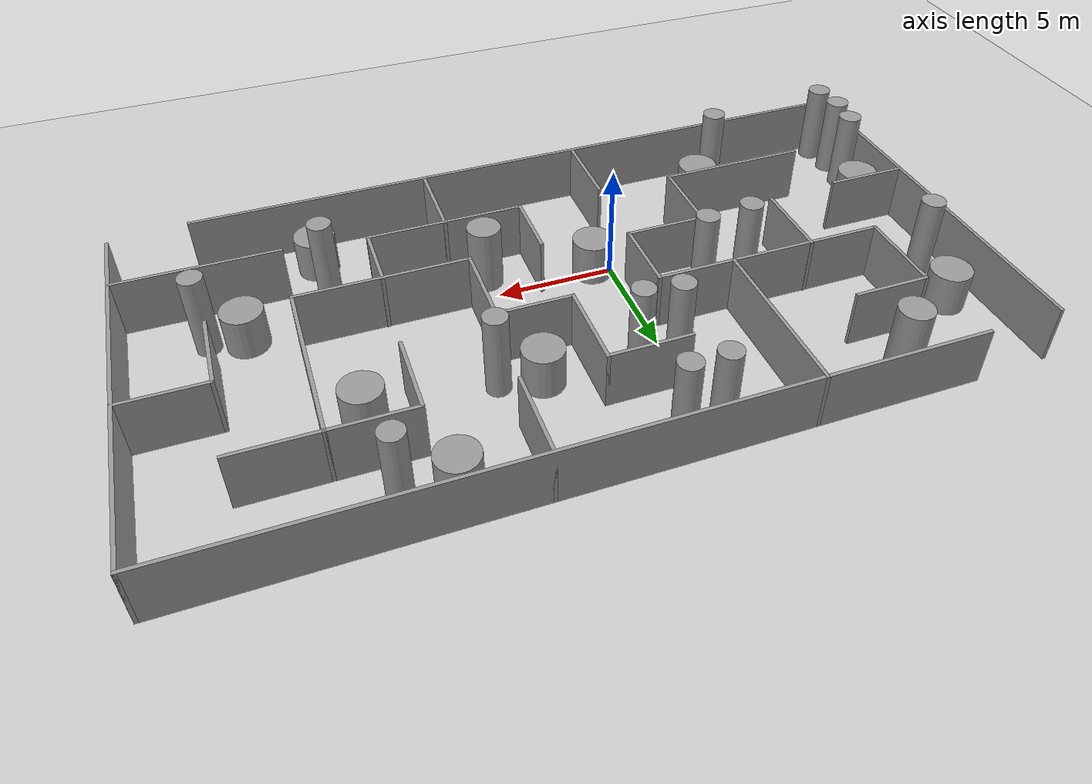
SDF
<sdf version="1.7">
 <world name="default">
  <model name="ground_plane">
   <static>1</static>
   <link name="link">
    <collision name="collision">
     <geometry><plane><normal>0 0 1</normal><size>100 100</size></plane></geometry>
     <surface>
      <contact><collide_bitmask>65535</collide_bitmask></contact>
      <friction><ode><mu>100</mu><mu2>50</mu2></ode></friction>
     </surface>
    </collision>
    <visual name="visual">
     <cast_shadows>0</cast_shadows>
     <geometry><plane><normal>0 0 1</normal><size>100 100</size></plane></geometry>
     <material>
      <script><uri>file://media/materials/scripts/gazebo.material</uri><name>Gazebo/Grey</name></script>
     </material>
    </visual>
   </link>
  </model>
  <light name="sun" type="directional">
   <pose>0 0 10 0 -0 0</pose>
   <diffuse>0.8 0.8 0.8 1</diffuse>
   <specular>0.2 0.2 0.2 1</specular>
   <attenuation>
    <range>1000</range>
    <constant>0.9</constant>
    <linear>0.01</linear>
    <quadratic>0.001</quadratic>
   </attenuation>
   <direction>-0.5 0.1 -0.9</direction>
   <spot><inner_angle>0</inner_angle><outer_angle>0</outer_angle><falloff>0</falloff></spot>
  </light>
  <gravity>0 0 -9.8</gravity>
  <magnetic_field>6e-06 2.3e-05 -4.2e-05</magnetic_field>
  <atmosphere type="adiabatic"/>
  <physics type="ode">
   <max_step_size>0.001</max_step_size>
   <real_time_factor>1</real_time_factor>
   <real_time_update_rate>1000</real_time_update_rate>
  </physics>
  <scene><ambient>0.4 0.4 0.4 1</ambient><background>0.7 0.7 0.7 1</background><shadows>1</shadows></scene>
  <spherical_coordinates>
   <surface_model>EARTH_WGS84</surface_model>
   <latitude_deg>0</latitude_deg>
   <longitude_deg>0</longitude_deg>
   <elevation>0</elevation>
   <heading_deg>0</heading_deg>
  </spherical_coordinates>
  <model name="maze3">
   <pose>3.0344 2.45345 0 0 -0 0</pose>
   <link name="Wall_115">
    <collision name="Wall_115_Collision">
     <geometry><box><size>17.25 0.15 2.5</size></box></geometry>
     <pose>0 0 1.25 0 -0 0</pose>
    </collision>
    <visual name="Wall_115_Visual">
     <pose>0 0 1.25 0 -0 0</pose>
     <geometry><box><size>17.25 0.15 2.5</size></box></geometry>
     <material>
      <script><uri>file://media/materials/scripts/gazebo.material</uri><name>Gazebo/Grey</name></script>
      <ambient>1 1 1 1</ambient>
     </material>
     <meta><layer>0</layer></meta>
    </visual>
    <pose>-16.9493 -0.060341 0 0 -0 -1.5708</pose>
   </link>
   <link name="Wall_116">
    <collision name="Wall_116_Collision">
     <geometry><box><size>30.75 0.15 2.5</size></box></geometry>
     <pose>0 0 1.25 0 -0 0</pose>
    </collision>
    <visual name="Wall_116_Visual">
     <pose>0 0 1.25 0 -0 0</pose>
     <geometry><box><size>30.75 0.15 2.5</size></box></geometry>
     <material>
      <script><uri>file://media/materials/scripts/gazebo.material</uri><name>Gazebo/Grey</name></script>
      <ambient>1 1 1 1</ambient>
     </material>
     <meta><layer>0</layer></meta>
    </visual>
    <pose>-1.64931 -8.61034 0 0 -0 0</pose>
   </link>
   <link name="Wall_118">
    <collision name="Wall_118_Collision">
     <geometry><box><size>30.75 0.15 2.5</size></box></geometry>
     <pose>0 0 1.25 0 -0 0</pose>
    </collision>
    <visual name="Wall_118_Visual">
     <pose>0 0 1.25 0 -0 0</pose>
     <geometry><box><size>30.75 0.15 2.5</size></box></geometry>
     <material>
      <script><uri>file://media/materials/scripts/gazebo.material</uri><name>Gazebo/Grey</name></script>
      <ambient>1 1 1 1</ambient>
     </material>
     <meta><layer>0</layer></meta>
    </visual>
    <pose>1.64931 8.61034 0 0 -0 0</pose>
   </link>
   <link name="Wall_119">
    <collision name="Wall_119_Collision">
     <geometry><box><size>17 0.15 2.5</size></box></geometry>
     <pose>0 0 1.25 0 -0 0</pose>
    </collision>
    <visual name="Wall_119_Visual">
     <pose>0 0 1.25 0 -0 0</pose>
     <geometry><box><size>17 0.15 2.5</size></box></geometry>
     <material>
      <script><uri>file://media/materials/scripts/gazebo.material</uri><name>Gazebo/Grey</name></script>
      <ambient>1 1 1 1</ambient>
     </material>
     <meta><layer>0</layer></meta>
    </visual>
    <pose>16.9493 0.185341 0 0 -0 -1.5708</pose>
   </link>
   <link name="Wall_121">
    <collision name="Wall_121_Collision">
     <geometry><box><size>3.5 0.15 2.5</size></box></geometry>
     <pose>0 0 1.25 0 -0 0</pose>
    </collision>
    <visual name="Wall_121_Visual">
     <pose>0 0 1.25 0 -0 0</pose>
     <geometry><box><size>3.5 0.15 2.5</size></box></geometry>
     <material>
      <script><uri>file://media/materials/scripts/gazebo.material</uri><name>Gazebo/Grey</name></script>
      <ambient>1 1 1 1</ambient>
     </material>
     <meta><layer>0</layer></meta>
    </visual>
    <pose>-15.1939 -2.00963 0 0 -0 0</pose>
   </link>
   <link name="Wall_123">
    <collision name="Wall_123_Collision">
     <geometry><box><size>6.5 0.15 2.5</size></box></geometry>
     <pose>0 0 1.25 0 -0 0</pose>
    </collision>
    <visual name="Wall_123_Visual">
     <pose>0 0 1.25 0 -0 0</pose>
     <geometry><box><size>6.5 0.15 2.5</size></box></geometry>
     <material>
      <script><uri>file://media/materials/scripts/gazebo.material</uri><name>Gazebo/Grey</name></script>
      <ambient>1 1 1 1</ambient>
     </material>
     <meta><layer>0</layer></meta>
    </visual>
    <pose>-9.99296 -4.94621 0 0 -0 0</pose>
   </link>
   <link name="Wall_124">
    <collision name="Wall_124_Collision">
     <geometry><box><size>3.5 0.15 2.5</size></box></geometry>
     <pose>0 0 1.25 0 -0 0</pose>
    </collision>
    <visual name="Wall_124_Visual">
     <pose>0 0 1.25 0 -0 0</pose>
     <geometry><box><size>3.5 0.15 2.5</size></box></geometry>
     <material>
      <script><uri>file://media/materials/scripts/gazebo.material</uri><name>Gazebo/Grey</name></script>
      <ambient>1 1 1 1</ambient>
     </material>
     <meta><layer>0</layer></meta>
    </visual>
    <pose>-6.81796 -3.27121 0 0 -0 1.5708</pose>
   </link>
   <link name="Wall_125">
    <collision name="Wall_125_Collision">
     <geometry><box><size>3.5 0.15 2.5</size></box></geometry>
     <pose>0 0 1.25 0 -0 0</pose>
    </collision>
    <visual name="Wall_125_Visual">
     <pose>0 0 1.25 0 -0 0</pose>
     <geometry><box><size>3.5 0.15 2.5</size></box></geometry>
     <material>
      <script><uri>file://media/materials/scripts/gazebo.material</uri><name>Gazebo/Grey</name></script>
      <ambient>1 1 1 1</ambient>
     </material>
     <meta><layer>0</layer></meta>
    </visual>
    <pose>-5.14296 -1.59621 0 0 -0 0</pose>
   </link>
   <link name="Wall_126">
    <collision name="Wall_126_Collision">
     <geometry><box><size>3.25 0.15 2.5</size></box></geometry>
     <pose>0 0 1.25 0 -0 0</pose>
    </collision>
    <visual name="Wall_126_Visual">
     <pose>0 0 1.25 0 -0 0</pose>
     <geometry><box><size>3.25 0.15 2.5</size></box></geometry>
     <material>
      <script><uri>file://media/materials/scripts/gazebo.material</uri><name>Gazebo/Grey</name></script>
      <ambient>1 1 1 1</ambient>
     </material>
     <meta><layer>0</layer></meta>
    </visual>
    <pose>-3.46796 -0.046207 0 0 -0 1.5708</pose>
   </link>
   <link name="Wall_127">
    <collision name="Wall_127_Collision">
     <geometry><box><size>10 0.15 2.5</size></box></geometry>
     <pose>0 0 1.25 0 -0 0</pose>
    </collision>
    <visual name="Wall_127_Visual">
     <pose>0 0 1.25 0 -0 0</pose>
     <geometry><box><size>10 0.15 2.5</size></box></geometry>
     <material>
      <script><uri>file://media/materials/scripts/gazebo.material</uri><name>Gazebo/Grey</name></script>
      <ambient>1 1 1 1</ambient>
     </material>
     <meta><layer>0</layer></meta>
    </visual>
    <pose>-8.39296 1.50379 0 0 -0 3.14159</pose>
   </link>
   <link name="Wall_128">
    <collision name="Wall_128_Collision">
     <geometry><box><size>3.75 0.15 2.5</size></box></geometry>
     <pose>0 0 1.25 0 -0 0</pose>
    </collision>
    <visual name="Wall_128_Visual">
     <pose>0 0 1.25 0 -0 0</pose>
     <geometry><box><size>3.75 0.15 2.5</size></box></geometry>
     <material>
      <script><uri>file://media/materials/scripts/gazebo.material</uri><name>Gazebo/Grey</name></script>
      <ambient>1 1 1 1</ambient>
     </material>
     <meta><layer>0</layer></meta>
    </visual>
    <pose>-13.318 3.30379 0 0 -0 1.5708</pose>
   </link>
   <link name="Wall_129">
    <collision name="Wall_129_Collision">
     <geometry><box><size>3.25 0.15 2.5</size></box></geometry>
     <pose>0 0 1.25 0 -0 0</pose>
    </collision>
    <visual name="Wall_129_Visual">
     <pose>0 0 1.25 0 -0 0</pose>
     <geometry><box><size>3.25 0.15 2.5</size></box></geometry>
     <material>
      <script><uri>file://media/materials/scripts/gazebo.material</uri><name>Gazebo/Grey</name></script>
      <ambient>1 1 1 1</ambient>
     </material>
     <meta><layer>0</layer></meta>
    </visual>
    <pose>-11.768 5.10379 0 0 -0 0</pose>
   </link>
   <link name="Wall_131">
    <collision name="Wall_131_Collision">
     <geometry><box><size>3.5 0.15 2.5</size></box></geometry>
     <pose>0 0 1.25 0 -0 0</pose>
    </collision>
    <visual name="Wall_131_Visual">
     <pose>0 0 1.25 0 -0 0</pose>
     <geometry><box><size>3.5 0.15 2.5</size></box></geometry>
     <material>
      <script><uri>file://media/materials/scripts/gazebo.material</uri><name>Gazebo/Grey</name></script>
      <ambient>1 1 1 1</ambient>
     </material>
     <meta><layer>0</layer></meta>
    </visual>
    <pose>-10.2716 -0.144636 0 0 -0 -1.5708</pose>
   </link>
   <link name="Wall_133">
    <collision name="Wall_133_Collision">
     <geometry><box><size>7.25 0.15 2.5</size></box></geometry>
     <pose>0 0 1.25 0 -0 0</pose>
    </collision>
    <visual name="Wall_133_Visual">
     <pose>0 0 1.25 0 -0 0</pose>
     <geometry><box><size>7.25 0.15 2.5</size></box></geometry>
     <material>
      <script><uri>file://media/materials/scripts/gazebo.material</uri><name>Gazebo/Grey</name></script>
      <ambient>1 1 1 1</ambient>
     </material>
     <meta><layer>0</layer></meta>
    </visual>
    <pose>-6.73162 5.06034 0 0 -0 -1.5708</pose>
   </link>
   <link name="Wall_135">
    <collision name="Wall_135_Collision">
     <geometry><box><size>3.75 0.15 2.5</size></box></geometry>
     <pose>0 0 1.25 0 -0 0</pose>
    </collision>
    <visual name="Wall_135_Visual">
     <pose>0 0 1.25 0 -0 0</pose>
     <geometry><box><size>3.75 0.15 2.5</size></box></geometry>
     <material>
      <script><uri>file://media/materials/scripts/gazebo.material</uri><name>Gazebo/Grey</name></script>
      <ambient>1 1 1 1</ambient>
     </material>
     <meta><layer>0</layer></meta>
    </visual>
    <pose>3.44585 6.81034 0 0 -0 -1.5708</pose>
   </link>
   <link name="Wall_137">
    <collision name="Wall_137_Collision">
     <geometry><box><size>3.5 0.15 2.5</size></box></geometry>
     <pose>0 0 1.25 0 -0 0</pose>
    </collision>
    <visual name="Wall_137_Visual">
     <pose>0 0 1.25 0 -0 0</pose>
     <geometry><box><size>3.5 0.15 2.5</size></box></geometry>
     <material>
      <script><uri>file://media/materials/scripts/gazebo.material</uri><name>Gazebo/Grey</name></script>
      <ambient>1 1 1 1</ambient>
     </material>
     <meta><layer>0</layer></meta>
    </visual>
    <pose>-1.55686 4.9899 0 0 -0 0</pose>
   </link>
   <link name="Wall_138">
    <collision name="Wall_138_Collision">
     <geometry><box><size>3.75 0.15 2.5</size></box></geometry>
     <pose>0 0 1.25 0 -0 0</pose>
    </collision>
    <visual name="Wall_138_Visual">
     <pose>0 0 1.25 0 -0 0</pose>
     <geometry><box><size>3.75 0.15 2.5</size></box></geometry>
     <material>
      <script><uri>file://media/materials/scripts/gazebo.material</uri><name>Gazebo/Grey</name></script>
      <ambient>1 1 1 1</ambient>
     </material>
     <meta><layer>0</layer></meta>
    </visual>
    <pose>0.118143 3.1899 0 0 -0 -1.5708</pose>
   </link>
   <link name="Wall_139">
    <collision name="Wall_139_Collision">
     <geometry><box><size>3.25 0.15 2.5</size></box></geometry>
     <pose>0 0 1.25 0 -0 0</pose>
    </collision>
    <visual name="Wall_139_Visual">
     <pose>0 0 1.25 0 -0 0</pose>
     <geometry><box><size>3.25 0.15 2.5</size></box></geometry>
     <material>
      <script><uri>file://media/materials/scripts/gazebo.material</uri><name>Gazebo/Grey</name></script>
      <ambient>1 1 1 1</ambient>
     </material>
     <meta><layer>0</layer></meta>
    </visual>
    <pose>1.66814 1.3899 0 0 -0 0</pose>
   </link>
   <link name="Wall_140">
    <collision name="Wall_140_Collision">
     <geometry><box><size>3.75 0.15 2.5</size></box></geometry>
     <pose>0 0 1.25 0 -0 0</pose>
    </collision>
    <visual name="Wall_140_Visual">
     <pose>0 0 1.25 0 -0 0</pose>
     <geometry><box><size>3.75 0.15 2.5</size></box></geometry>
     <material>
      <script><uri>file://media/materials/scripts/gazebo.material</uri><name>Gazebo/Grey</name></script>
      <ambient>1 1 1 1</ambient>
     </material>
     <meta><layer>0</layer></meta>
    </visual>
    <pose>3.21814 -0.410102 0 0 -0 -1.5708</pose>
   </link>
   <link name="Wall_141">
    <collision name="Wall_141_Collision">
     <geometry><box><size>7.25 0.15 2.5</size></box></geometry>
     <pose>0 0 1.25 0 -0 0</pose>
    </collision>
    <visual name="Wall_141_Visual">
     <pose>0 0 1.25 0 -0 0</pose>
     <geometry><box><size>7.25 0.15 2.5</size></box></geometry>
     <material>
      <script><uri>file://media/materials/scripts/gazebo.material</uri><name>Gazebo/Grey</name></script>
      <ambient>1 1 1 1</ambient>
     </material>
     <meta><layer>0</layer></meta>
    </visual>
    <pose>6.76814 -2.2101 0 0 -0 0</pose>
   </link>
   <link name="Wall_142">
    <collision name="Wall_142_Collision">
     <geometry><box><size>7.5 0.15 2.5</size></box></geometry>
     <pose>0 0 1.25 0 -0 0</pose>
    </collision>
    <visual name="Wall_142_Visual">
     <pose>0 0 1.25 0 -0 0</pose>
     <geometry><box><size>7.5 0.15 2.5</size></box></geometry>
     <material>
      <script><uri>file://media/materials/scripts/gazebo.material</uri><name>Gazebo/Grey</name></script>
      <ambient>1 1 1 1</ambient>
     </material>
     <meta><layer>0</layer></meta>
    </visual>
    <pose>10.3181 1.4649 0 0 -0 1.5708</pose>
   </link>
   <link name="Wall_143">
    <collision name="Wall_143_Collision">
     <geometry><box><size>3.5 0.15 2.5</size></box></geometry>
     <pose>0 0 1.25 0 -0 0</pose>
    </collision>
    <visual name="Wall_143_Visual">
     <pose>0 0 1.25 0 -0 0</pose>
     <geometry><box><size>3.5 0.15 2.5</size></box></geometry>
     <material>
      <script><uri>file://media/materials/scripts/gazebo.material</uri><name>Gazebo/Grey</name></script>
      <ambient>1 1 1 1</ambient>
     </material>
     <meta><layer>0</layer></meta>
    </visual>
    <pose>8.64314 5.1399 0 0 -0 3.14159</pose>
   </link>
   <link name="Wall_144">
    <collision name="Wall_144_Collision">
     <geometry><box><size>3.5 0.15 2.5</size></box></geometry>
     <pose>0 0 1.25 0 -0 0</pose>
    </collision>
    <visual name="Wall_144_Visual">
     <pose>0 0 1.25 0 -0 0</pose>
     <geometry><box><size>3.5 0.15 2.5</size></box></geometry>
     <material>
      <script><uri>file://media/materials/scripts/gazebo.material</uri><name>Gazebo/Grey</name></script>
      <ambient>1 1 1 1</ambient>
     </material>
     <meta><layer>0</layer></meta>
    </visual>
    <pose>6.96814 3.4649 0 0 -0 -1.5708</pose>
   </link>
   <link name="Wall_146">
    <collision name="Wall_146_Collision">
     <geometry><box><size>3.5 0.15 2.5</size></box></geometry>
     <pose>0 0 1.25 0 -0 0</pose>
    </collision>
    <visual name="Wall_146_Visual">
     <pose>0 0 1.25 0 -0 0</pose>
     <geometry><box><size>3.5 0.15 2.5</size></box></geometry>
     <material>
      <script><uri>file://media/materials/scripts/gazebo.material</uri><name>Gazebo/Grey</name></script>
      <ambient>1 1 1 1</ambient>
     </material>
     <meta><layer>0</layer></meta>
    </visual>
    <pose>11.9931 5.1399 0 0 -0 0</pose>
   </link>
   <link name="Wall_148">
    <collision name="Wall_148_Collision">
     <geometry><box><size>3.5 0.15 2.5</size></box></geometry>
     <pose>0 0 1.25 0 -0 0</pose>
    </collision>
    <visual name="Wall_148_Visual">
     <pose>0 0 1.25 0 -0 0</pose>
     <geometry><box><size>3.5 0.15 2.5</size></box></geometry>
     <material>
      <script><uri>file://media/materials/scripts/gazebo.material</uri><name>Gazebo/Grey</name></script>
      <ambient>1 1 1 1</ambient>
     </material>
     <meta><layer>0</layer></meta>
    </visual>
    <pose>-3.51345 -6.78212 0 0 -0 -1.5708</pose>
   </link>
   <link name="Wall_150">
    <collision name="Wall_150_Collision">
     <geometry><box><size>6.75 0.15 2.5</size></box></geometry>
     <pose>0 0 1.25 0 -0 0</pose>
    </collision>
    <visual name="Wall_150_Visual">
     <pose>0 0 1.25 0 -0 0</pose>
     <geometry><box><size>6.75 0.15 2.5</size></box></geometry>
     <material>
      <script><uri>file://media/materials/scripts/gazebo.material</uri><name>Gazebo/Grey</name></script>
      <ambient>1 1 1 1</ambient>
     </material>
     <meta><layer>0</layer></meta>
    </visual>
    <pose>13.5845 -5.3887 0 0 -0 0</pose>
   </link>
   <link name="Wall_152">
    <collision name="Wall_152_Collision">
     <geometry><box><size>3.5 0.15 2.5</size></box></geometry>
     <pose>0 0 1.25 0 -0 0</pose>
    </collision>
    <visual name="Wall_152_Visual">
     <pose>0 0 1.25 0 -0 0</pose>
     <geometry><box><size>3.5 0.15 2.5</size></box></geometry>
     <material>
      <script><uri>file://media/materials/scripts/gazebo.material</uri><name>Gazebo/Grey</name></script>
      <ambient>1 1 1 1</ambient>
     </material>
     <meta><layer>0</layer></meta>
    </visual>
    <pose>13.5831 -0.173717 0 0 -0 1.5708</pose>
   </link>
   <link name="Wall_153">
    <collision name="Wall_153_Collision">
     <geometry><box><size>3.5 0.15 2.5</size></box></geometry>
     <pose>0 0 1.25 0 -0 0</pose>
    </collision>
    <visual name="Wall_153_Visual">
     <pose>0 0 1.25 0 -0 0</pose>
     <geometry><box><size>3.5 0.15 2.5</size></box></geometry>
     <material>
      <script><uri>file://media/materials/scripts/gazebo.material</uri><name>Gazebo/Grey</name></script>
      <ambient>1 1 1 1</ambient>
     </material>
     <meta><layer>0</layer></meta>
    </visual>
    <pose>15.2581 1.50128 0 0 -0 0</pose>
   </link>
   <link name="Wall_155">
    <collision name="Wall_155_Collision">
     <geometry><box><size>3 0.15 2.5</size></box></geometry>
     <pose>0 0 1.25 0 -0 0</pose>
    </collision>
    <visual name="Wall_155_Visual">
     <pose>0 0 1.25 0 -0 0</pose>
     <geometry><box><size>3 0.15 2.5</size></box></geometry>
     <material>
      <script><uri>file://media/materials/scripts/gazebo.material</uri><name>Gazebo/Grey</name></script>
      <ambient>1 1 1 1</ambient>
     </material>
     <meta><layer>0</layer></meta>
    </visual>
    <pose>6.7847 -3.59553 0 0 -0 -1.5708</pose>
   </link>
   <link name="Wall_156">
    <collision name="Wall_156_Collision">
     <geometry><box><size>6.75 0.15 2.5</size></box></geometry>
     <pose>0 0 1.25 0 -0 0</pose>
    </collision>
    <visual name="Wall_156_Visual">
     <pose>0 0 1.25 0 -0 0</pose>
     <geometry><box><size>6.75 0.15 2.5</size></box></geometry>
     <material>
      <script><uri>file://media/materials/scripts/gazebo.material</uri><name>Gazebo/Grey</name></script>
      <ambient>1 1 1 1</ambient>
     </material>
     <meta><layer>0</layer></meta>
    </visual>
    <pose>3.4847 -5.02053 0 0 -0 3.14159</pose>
   </link>
   <link name="Wall_157">
    <collision name="Wall_157_Collision">
     <geometry><box><size>3 0.15 2.5</size></box></geometry>
     <pose>0 0 1.25 0 -0 0</pose>
    </collision>
    <visual name="Wall_157_Visual">
     <pose>0 0 1.25 0 -0 0</pose>
     <geometry><box><size>3 0.15 2.5</size></box></geometry>
     <material>
      <script><uri>file://media/materials/scripts/gazebo.material</uri><name>Gazebo/Grey</name></script>
      <ambient>1 1 1 1</ambient>
     </material>
     <meta><layer>0</layer></meta>
    </visual>
    <pose>0.184702 -3.59553 0 0 -0 1.5708</pose>
   </link>
   <link name="Wall_159">
    <collision name="Wall_159_Collision">
     <geometry><box><size>3.75 0.15 2.5</size></box></geometry>
     <pose>0 0 1.25 0 -0 0</pose>
    </collision>
    <visual name="Wall_159_Visual">
     <pose>0 0 1.25 0 -0 0</pose>
     <geometry><box><size>3.75 0.15 2.5</size></box></geometry>
     <material>
      <script><uri>file://media/materials/scripts/gazebo.material</uri><name>Gazebo/Grey</name></script>
      <ambient>1 1 1 1</ambient>
     </material>
     <meta><layer>0</layer></meta>
    </visual>
    <pose>3.5263 -6.76665 0 0 -0 1.5708</pose>
   </link>
   <static>1</static>
  </model>
  <model name="big_cylinder">
   <link name="link_6">
    <inertial>
     <mass>5.40188</mass>
     <inertia><ixx>2.45932</ixx><ixy>0</ixy><ixz>0</ixz><iyy>2.45932</iyy><iyz>0</iyz><izz>2.03968</izz></inertia>
    </inertial>
    <pose>3e-06 3e-06 0 0 -0 0</pose>
    <visual name="visual">
     <geometry><cylinder><radius>0.869008</radius><length>1.78822</length></cylinder></geometry>
     <material>
      <lighting>1</lighting>
      <script><uri>file://media/materials/scripts/gazebo.material</uri><name>Gazebo/Grey</name></script>
      <shader type="pixel"/>
     </material>
    </visual>
    <collision name="collision">
     <geometry><cylinder><radius>0.869008</radius><length>1.78822</length></cylinder></geometry>
     <surface>
      <friction>
       <ode><mu>1</mu><mu2>1</mu2><fdir1>0 0 0</fdir1><slip1>0</slip1><slip2>0</slip2></ode>
       <torsional>
        <coefficient>1</coefficient>
        <patch_radius>0</patch_radius>
        <surface_radius>0</surface_radius>
        <use_patch_radius>1</use_patch_radius>
        <ode><slip>0</slip></ode>
       </torsional>
      </friction>
      <bounce><restitution_coefficient>0</restitution_coefficient><threshold>1e+06</threshold></bounce>
      <contact>
       <collide_without_contact>0</collide_without_contact>
       <collide_without_contact_bitmask>1</collide_without_contact_bitmask>
       <collide_bitmask>1</collide_bitmask>
       <ode>
        <soft_cfm>0</soft_cfm>
        <soft_erp>0.2</soft_erp>
        <kp>1e+13</kp>
        <kd>1</kd>
        <max_vel>0.01</max_vel>
        <min_depth>0</min_depth>
       </ode>
       <bullet>
        <split_impulse>1</split_impulse>
        <split_impulse_penetration_threshold>-0.01</split_impulse_penetration_threshold>
        <soft_cfm>0</soft_cfm>
        <soft_erp>0.2</soft_erp>
        <kp>1e+13</kp>
        <kd>1</kd>
       </bullet>
      </contact>
     </surface>
    </collision>
   </link>
   <static>0</static>
   <pose>11.8521 -4.46733 0.89411 0 -0 0</pose>
  </model>
  <model name="big_cylinder_0">
   <link name="link_6">
    <inertial>
     <mass>5.40188</mass>
     <inertia><ixx>2.45932</ixx><ixy>0</ixy><ixz>0</ixz><iyy>2.45932</iyy><iyz>0</iyz><izz>2.03968</izz></inertia>
    </inertial>
    <pose>3e-06 3e-06 0 0 -0 0</pose>
    <visual name="visual">
     <geometry><cylinder><radius>0.869008</radius><length>1.78822</length></cylinder></geometry>
     <material>
      <lighting>1</lighting>
      <script><uri>file://media/materials/scripts/gazebo.material</uri><name>Gazebo/Grey</name></script>
      <shader type="pixel"/>
     </material>
    </visual>
    <collision name="collision">
     <geometry><cylinder><radius>0.869008</radius><length>1.78822</length></cylinder></geometry>
     <surface>
      <friction>
       <ode><mu>1</mu><mu2>1</mu2><fdir1>0 0 0</fdir1><slip1>0</slip1><slip2>0</slip2></ode>
       <torsional>
        <coefficient>1</coefficient>
        <patch_radius>0</patch_radius>
        <surface_radius>0</surface_radius>
        <use_patch_radius>1</use_patch_radius>
        <ode><slip>0</slip></ode>
       </torsional>
      </friction>
      <bounce><restitution_coefficient>0</restitution_coefficient><threshold>1e+06</threshold></bounce>
      <contact>
       <collide_without_contact>0</collide_without_contact>
       <collide_without_contact_bitmask>1</collide_without_contact_bitmask>
       <collide_bitmask>1</collide_bitmask>
       <ode>
        <soft_cfm>0</soft_cfm>
        <soft_erp>0.2</soft_erp>
        <kp>1e+13</kp>
        <kd>1</kd>
        <max_vel>0.01</max_vel>
        <min_depth>0</min_depth>
       </ode>
       <bullet>
        <split_impulse>1</split_impulse>
        <split_impulse_penetration_threshold>-0.01</split_impulse_penetration_threshold>
        <soft_cfm>0</soft_cfm>
        <soft_erp>0.2</soft_erp>
        <kp>1e+13</kp>
        <kd>1</kd>
       </bullet>
      </contact>
     </surface>
    </collision>
   </link>
   <static>0</static>
   <pose>15.3037 -0.526272 0.89411 0 -0 0</pose>
  </model>
  <model name="big_cylinder_1">
   <link name="link_6">
    <inertial>
     <mass>5.40188</mass>
     <inertia><ixx>2.45932</ixx><ixy>0</ixy><ixz>0</ixz><iyy>2.45932</iyy><iyz>0</iyz><izz>2.03968</izz></inertia>
    </inertial>
    <pose>3e-06 3e-06 0 0 -0 0</pose>
    <visual name="visual">
     <geometry><cylinder><radius>0.869008</radius><length>1.78822</length></cylinder></geometry>
     <material>
      <lighting>1</lighting>
      <script><uri>file://media/materials/scripts/gazebo.material</uri><name>Gazebo/Grey</name></script>
      <shader type="pixel"/>
     </material>
    </visual>
    <collision name="collision">
     <geometry><cylinder><radius>0.869008</radius><length>1.78822</length></cylinder></geometry>
     <surface>
      <friction>
       <ode><mu>1</mu><mu2>1</mu2><fdir1>0 0 0</fdir1><slip1>0</slip1><slip2>0</slip2></ode>
       <torsional>
        <coefficient>1</coefficient>
        <patch_radius>0</patch_radius>
        <surface_radius>0</surface_radius>
        <use_patch_radius>1</use_patch_radius>
        <ode><slip>0</slip></ode>
       </torsional>
      </friction>
      <bounce><restitution_coefficient>0</restitution_coefficient><threshold>1e+06</threshold></bounce>
      <contact>
       <collide_without_contact>0</collide_without_contact>
       <collide_without_contact_bitmask>1</collide_without_contact_bitmask>
       <collide_bitmask>1</collide_bitmask>
       <ode>
        <soft_cfm>0</soft_cfm>
        <soft_erp>0.2</soft_erp>
        <kp>1e+13</kp>
        <kd>1</kd>
        <max_vel>0.01</max_vel>
        <min_depth>0</min_depth>
       </ode>
       <bullet>
        <split_impulse>1</split_impulse>
        <split_impulse_penetration_threshold>-0.01</split_impulse_penetration_threshold>
        <soft_cfm>0</soft_cfm>
        <soft_erp>0.2</soft_erp>
        <kp>1e+13</kp>
        <kd>1</kd>
       </bullet>
      </contact>
     </surface>
    </collision>
   </link>
   <static>0</static>
   <pose>9.35016 9.46345 0.89411 0 -0 0</pose>
  </model>
  <model name="big_cylinder_2">
   <link name="link_6">
    <inertial>
     <mass>5.40188</mass>
     <inertia><ixx>2.45932</ixx><ixy>0</ixy><ixz>0</ixz><iyy>2.45932</iyy><iyz>0</iyz><izz>2.03968</izz></inertia>
    </inertial>
    <pose>3e-06 3e-06 0 0 -0 0</pose>
    <visual name="visual">
     <geometry><cylinder><radius>0.869008</radius><length>1.78822</length></cylinder></geometry>
     <material>
      <lighting>1</lighting>
      <script><uri>file://media/materials/scripts/gazebo.material</uri><name>Gazebo/Grey</name></script>
      <shader type="pixel"/>
     </material>
    </visual>
    <collision name="collision">
     <geometry><cylinder><radius>0.869008</radius><length>1.78822</length></cylinder></geometry>
     <surface>
      <friction>
       <ode><mu>1</mu><mu2>1</mu2><fdir1>0 0 0</fdir1><slip1>0</slip1><slip2>0</slip2></ode>
       <torsional>
        <coefficient>1</coefficient>
        <patch_radius>0</patch_radius>
        <surface_radius>0</surface_radius>
        <use_patch_radius>1</use_patch_radius>
        <ode><slip>0</slip></ode>
       </torsional>
      </friction>
      <bounce><restitution_coefficient>0</restitution_coefficient><threshold>1e+06</threshold></bounce>
      <contact>
       <collide_without_contact>0</collide_without_contact>
       <collide_without_contact_bitmask>1</collide_without_contact_bitmask>
       <collide_bitmask>1</collide_bitmask>
       <ode>
        <soft_cfm>0</soft_cfm>
        <soft_erp>0.2</soft_erp>
        <kp>1e+13</kp>
        <kd>1</kd>
        <max_vel>0.01</max_vel>
        <min_depth>0</min_depth>
       </ode>
       <bullet>
        <split_impulse>1</split_impulse>
        <split_impulse_penetration_threshold>-0.01</split_impulse_penetration_threshold>
        <soft_cfm>0</soft_cfm>
        <soft_erp>0.2</soft_erp>
        <kp>1e+13</kp>
        <kd>1</kd>
       </bullet>
      </contact>
     </surface>
    </collision>
   </link>
   <static>0</static>
   <pose>4.96221 5.53852 0.89411 0 -0 0</pose>
  </model>
  <model name="long_cylinder">
   <link name="link_5">
    <inertial>
     <mass>3.60259</mass>
     <inertia><ixx>4.12154</ixx><ixy>0</ixy><ixz>0</ixz><iyy>4.12154</iyy><iyz>0</iyz><izz>0.450323</izz></inertia>
    </inertial>
    <pose>0 -2e-06 0 0 -0 0</pose>
    <visual name="visual">
     <geometry><cylinder><radius>0.5</radius><length>3.60259</length></cylinder></geometry>
     <material>
      <lighting>1</lighting>
      <script><uri>file://media/materials/scripts/gazebo.material</uri><name>Gazebo/Grey</name></script>
      <shader type="pixel"/>
      <emissive>0 0 0 1</emissive>
     </material>
    </visual>
    <collision name="collision">
     <geometry><cylinder><radius>0.5</radius><length>3.60258</length></cylinder></geometry>
     <surface>
      <friction>
       <ode><mu>1</mu><mu2>1</mu2><fdir1>0 0 0</fdir1><slip1>0</slip1><slip2>0</slip2></ode>
       <torsional>
        <coefficient>1</coefficient>
        <patch_radius>0</patch_radius>
        <surface_radius>0</surface_radius>
        <use_patch_radius>1</use_patch_radius>
        <ode><slip>0</slip></ode>
       </torsional>
      </friction>
      <bounce><restitution_coefficient>0</restitution_coefficient><threshold>1e+06</threshold></bounce>
      <contact>
       <collide_without_contact>0</collide_without_contact>
       <collide_without_contact_bitmask>1</collide_without_contact_bitmask>
       <collide_bitmask>1</collide_bitmask>
       <ode>
        <soft_cfm>0</soft_cfm>
        <soft_erp>0.2</soft_erp>
        <kp>1e+13</kp>
        <kd>1</kd>
        <max_vel>0.01</max_vel>
        <min_depth>0</min_depth>
       </ode>
       <bullet>
        <split_impulse>1</split_impulse>
        <split_impulse_penetration_threshold>-0.01</split_impulse_penetration_threshold>
        <soft_cfm>0</soft_cfm>
        <soft_erp>0.2</soft_erp>
        <kp>1e+13</kp>
        <kd>1</kd>
       </bullet>
      </contact>
     </surface>
    </collision>
   </link>
   <static>0</static>
   <pose>1.0868 9.76973 1.80129 0 -0 0</pose>
  </model>
  <model name="long_cylinder_0">
   <link name="link_5">
    <inertial>
     <mass>3.60259</mass>
     <inertia><ixx>4.12154</ixx><ixy>0</ixy><ixz>0</ixz><iyy>4.12154</iyy><iyz>0</iyz><izz>0.450323</izz></inertia>
    </inertial>
    <pose>0 -2e-06 0 0 -0 0</pose>
    <visual name="visual">
     <geometry><cylinder><radius>0.5</radius><length>3.60259</length></cylinder></geometry>
     <material>
      <lighting>1</lighting>
      <script><uri>file://media/materials/scripts/gazebo.material</uri><name>Gazebo/Grey</name></script>
      <shader type="pixel"/>
      <emissive>0 0 0 1</emissive>
     </material>
    </visual>
    <collision name="collision">
     <geometry><cylinder><radius>0.5</radius><length>3.60258</length></cylinder></geometry>
     <surface>
      <friction>
       <ode><mu>1</mu><mu2>1</mu2><fdir1>0 0 0</fdir1><slip1>0</slip1><slip2>0</slip2></ode>
       <torsional>
        <coefficient>1</coefficient>
        <patch_radius>0</patch_radius>
        <surface_radius>0</surface_radius>
        <use_patch_radius>1</use_patch_radius>
        <ode><slip>0</slip></ode>
       </torsional>
      </friction>
      <bounce><restitution_coefficient>0</restitution_coefficient><threshold>1e+06</threshold></bounce>
      <contact>
       <collide_without_contact>0</collide_without_contact>
       <collide_without_contact_bitmask>1</collide_without_contact_bitmask>
       <collide_bitmask>1</collide_bitmask>
       <ode>
        <soft_cfm>0</soft_cfm>
        <soft_erp>0.2</soft_erp>
        <kp>1e+13</kp>
        <kd>1</kd>
        <max_vel>0.01</max_vel>
        <min_depth>0</min_depth>
       </ode>
       <bullet>
        <split_impulse>1</split_impulse>
        <split_impulse_penetration_threshold>-0.01</split_impulse_penetration_threshold>
        <soft_cfm>0</soft_cfm>
        <soft_erp>0.2</soft_erp>
        <kp>1e+13</kp>
        <kd>1</kd>
       </bullet>
      </contact>
     </surface>
    </collision>
   </link>
   <static>0</static>
   <pose>1.01152 5.61061 1.80129 0 -0 0</pose>
  </model>
  <model name="big_cylinder_3">
   <link name="link_6">
    <inertial>
     <mass>5.40188</mass>
     <inertia><ixx>2.45932</ixx><ixy>0</ixy><ixz>0</ixz><iyy>2.45932</iyy><iyz>0</iyz><izz>2.03968</izz></inertia>
    </inertial>
    <pose>3e-06 3e-06 0 0 -0 0</pose>
    <visual name="visual">
     <geometry><cylinder><radius>0.869008</radius><length>1.78822</length></cylinder></geometry>
     <material>
      <lighting>1</lighting>
      <script><uri>file://media/materials/scripts/gazebo.material</uri><name>Gazebo/Grey</name></script>
      <shader type="pixel"/>
     </material>
    </visual>
    <collision name="collision">
     <geometry><cylinder><radius>0.869008</radius><length>1.78822</length></cylinder></geometry>
     <surface>
      <friction>
       <ode><mu>1</mu><mu2>1</mu2><fdir1>0 0 0</fdir1><slip1>0</slip1><slip2>0</slip2></ode>
       <torsional>
        <coefficient>1</coefficient>
        <patch_radius>0</patch_radius>
        <surface_radius>0</surface_radius>
        <use_patch_radius>1</use_patch_radius>
        <ode><slip>0</slip></ode>
       </torsional>
      </friction>
      <bounce><restitution_coefficient>0</restitution_coefficient><threshold>1e+06</threshold></bounce>
      <contact>
       <collide_without_contact>0</collide_without_contact>
       <collide_without_contact_bitmask>1</collide_without_contact_bitmask>
       <collide_bitmask>1</collide_bitmask>
       <ode>
        <soft_cfm>0</soft_cfm>
        <soft_erp>0.2</soft_erp>
        <kp>1e+13</kp>
        <kd>1</kd>
        <max_vel>0.01</max_vel>
        <min_depth>0</min_depth>
       </ode>
       <bullet>
        <split_impulse>1</split_impulse>
        <split_impulse_penetration_threshold>-0.01</split_impulse_penetration_threshold>
        <soft_cfm>0</soft_cfm>
        <soft_erp>0.2</soft_erp>
        <kp>1e+13</kp>
        <kd>1</kd>
       </bullet>
      </contact>
     </surface>
    </collision>
   </link>
   <static>0</static>
   <pose>0.750403 -0.209836 0.89411 0 -0 0</pose>
  </model>
  <model name="long_cylinder_1">
   <link name="link_5">
    <inertial>
     <mass>3.60259</mass>
     <inertia><ixx>4.12154</ixx><ixy>0</ixy><ixz>0</ixz><iyy>4.12154</iyy><iyz>0</iyz><izz>0.450323</izz></inertia>
    </inertial>
    <pose>0 -2e-06 0 0 -0 0</pose>
    <visual name="visual">
     <geometry><cylinder><radius>0.5</radius><length>3.60259</length></cylinder></geometry>
     <material>
      <lighting>1</lighting>
      <script><uri>file://media/materials/scripts/gazebo.material</uri><name>Gazebo/Grey</name></script>
      <shader type="pixel"/>
      <emissive>0 0 0 1</emissive>
     </material>
    </visual>
    <collision name="collision">
     <geometry><cylinder><radius>0.5</radius><length>3.60258</length></cylinder></geometry>
     <surface>
      <friction>
       <ode><mu>1</mu><mu2>1</mu2><fdir1>0 0 0</fdir1><slip1>0</slip1><slip2>0</slip2></ode>
       <torsional>
        <coefficient>1</coefficient>
        <patch_radius>0</patch_radius>
        <surface_radius>0</surface_radius>
        <use_patch_radius>1</use_patch_radius>
        <ode><slip>0</slip></ode>
       </torsional>
      </friction>
      <bounce><restitution_coefficient>0</restitution_coefficient><threshold>1e+06</threshold></bounce>
      <contact>
       <collide_without_contact>0</collide_without_contact>
       <collide_without_contact_bitmask>1</collide_without_contact_bitmask>
       <collide_bitmask>1</collide_bitmask>
       <ode>
        <soft_cfm>0</soft_cfm>
        <soft_erp>0.2</soft_erp>
        <kp>1e+13</kp>
        <kd>1</kd>
        <max_vel>0.01</max_vel>
        <min_depth>0</min_depth>
       </ode>
       <bullet>
        <split_impulse>1</split_impulse>
        <split_impulse_penetration_threshold>-0.01</split_impulse_penetration_threshold>
        <soft_cfm>0</soft_cfm>
        <soft_erp>0.2</soft_erp>
        <kp>1e+13</kp>
        <kd>1</kd>
       </bullet>
      </contact>
     </surface>
    </collision>
   </link>
   <static>0</static>
   <pose>-13.1256 -5.521 1.80129 0 -0 0</pose>
  </model>
  <model name="long_cylinder_2">
   <link name="link_5">
    <inertial>
     <mass>3.60259</mass>
     <inertia><ixx>4.12154</ixx><ixy>0</ixy><ixz>0</ixz><iyy>4.12154</iyy><iyz>0</iyz><izz>0.450323</izz></inertia>
    </inertial>
    <pose>0 -2e-06 0 0 -0 0</pose>
    <visual name="visual">
     <geometry><cylinder><radius>0.5</radius><length>3.60259</length></cylinder></geometry>
     <material>
      <lighting>1</lighting>
      <script><uri>file://media/materials/scripts/gazebo.material</uri><name>Gazebo/Grey</name></script>
      <shader type="pixel"/>
      <emissive>0 0 0 1</emissive>
     </material>
    </visual>
    <collision name="collision">
     <geometry><cylinder><radius>0.5</radius><length>3.60258</length></cylinder></geometry>
     <surface>
      <friction>
       <ode><mu>1</mu><mu2>1</mu2><fdir1>0 0 0</fdir1><slip1>0</slip1><slip2>0</slip2></ode>
       <torsional>
        <coefficient>1</coefficient>
        <patch_radius>0</patch_radius>
        <surface_radius>0</surface_radius>
        <use_patch_radius>1</use_patch_radius>
        <ode><slip>0</slip></ode>
       </torsional>
      </friction>
      <bounce><restitution_coefficient>0</restitution_coefficient><threshold>1e+06</threshold></bounce>
      <contact>
       <collide_without_contact>0</collide_without_contact>
       <collide_without_contact_bitmask>1</collide_without_contact_bitmask>
       <collide_bitmask>1</collide_bitmask>
       <ode>
        <soft_cfm>0</soft_cfm>
        <soft_erp>0.2</soft_erp>
        <kp>1e+13</kp>
        <kd>1</kd>
        <max_vel>0.01</max_vel>
        <min_depth>0</min_depth>
       </ode>
       <bullet>
        <split_impulse>1</split_impulse>
        <split_impulse_penetration_threshold>-0.01</split_impulse_penetration_threshold>
        <soft_cfm>0</soft_cfm>
        <soft_erp>0.2</soft_erp>
        <kp>1e+13</kp>
        <kd>1</kd>
       </bullet>
      </contact>
     </surface>
    </collision>
   </link>
   <static>0</static>
   <pose>-13.3092 -4.16594 1.80129 0 -0 0</pose>
  </model>
  <model name="long_cylinder_3">
   <link name="link_5">
    <inertial>
     <mass>3.60259</mass>
     <inertia><ixx>4.12154</ixx><ixy>0</ixy><ixz>0</ixz><iyy>4.12154</iyy><iyz>0</iyz><izz>0.450323</izz></inertia>
    </inertial>
    <pose>0 -2e-06 0 0 -0 0</pose>
    <visual name="visual">
     <geometry><cylinder><radius>0.5</radius><length>3.60259</length></cylinder></geometry>
     <material>
      <lighting>1</lighting>
      <script><uri>file://media/materials/scripts/gazebo.material</uri><name>Gazebo/Grey</name></script>
      <shader type="pixel"/>
      <emissive>0 0 0 1</emissive>
     </material>
    </visual>
    <collision name="collision">
     <geometry><cylinder><radius>0.5</radius><length>3.60258</length></cylinder></geometry>
     <surface>
      <friction>
       <ode><mu>1</mu><mu2>1</mu2><fdir1>0 0 0</fdir1><slip1>0</slip1><slip2>0</slip2></ode>
       <torsional>
        <coefficient>1</coefficient>
        <patch_radius>0</patch_radius>
        <surface_radius>0</surface_radius>
        <use_patch_radius>1</use_patch_radius>
        <ode><slip>0</slip></ode>
       </torsional>
      </friction>
      <bounce><restitution_coefficient>0</restitution_coefficient><threshold>1e+06</threshold></bounce>
      <contact>
       <collide_without_contact>0</collide_without_contact>
       <collide_without_contact_bitmask>1</collide_without_contact_bitmask>
       <collide_bitmask>1</collide_bitmask>
       <ode>
        <soft_cfm>0</soft_cfm>
        <soft_erp>0.2</soft_erp>
        <kp>1e+13</kp>
        <kd>1</kd>
        <max_vel>0.01</max_vel>
        <min_depth>0</min_depth>
       </ode>
       <bullet>
        <split_impulse>1</split_impulse>
        <split_impulse_penetration_threshold>-0.01</split_impulse_penetration_threshold>
        <soft_cfm>0</soft_cfm>
        <soft_erp>0.2</soft_erp>
        <kp>1e+13</kp>
        <kd>1</kd>
       </bullet>
      </contact>
     </surface>
    </collision>
   </link>
   <static>0</static>
   <pose>-13.1272 -2.76523 1.80129 0 -0 0</pose>
  </model>
  <model name="big_cylinder_4">
   <link name="link_6">
    <inertial>
     <mass>5.40188</mass>
     <inertia><ixx>2.45932</ixx><ixy>0</ixy><ixz>0</ixz><iyy>2.45932</iyy><iyz>0</iyz><izz>2.03968</izz></inertia>
    </inertial>
    <pose>3e-06 3e-06 0 0 -0 0</pose>
    <visual name="visual">
     <geometry><cylinder><radius>0.869008</radius><length>1.78822</length></cylinder></geometry>
     <material>
      <lighting>1</lighting>
      <script><uri>file://media/materials/scripts/gazebo.material</uri><name>Gazebo/Grey</name></script>
      <shader type="pixel"/>
     </material>
    </visual>
    <collision name="collision">
     <geometry><cylinder><radius>0.869008</radius><length>1.78822</length></cylinder></geometry>
     <surface>
      <friction>
       <ode><mu>1</mu><mu2>1</mu2><fdir1>0 0 0</fdir1><slip1>0</slip1><slip2>0</slip2></ode>
       <torsional>
        <coefficient>1</coefficient>
        <patch_radius>0</patch_radius>
        <surface_radius>0</surface_radius>
        <use_patch_radius>1</use_patch_radius>
        <ode><slip>0</slip></ode>
       </torsional>
      </friction>
      <bounce><restitution_coefficient>0</restitution_coefficient><threshold>1e+06</threshold></bounce>
      <contact>
       <collide_without_contact>0</collide_without_contact>
       <collide_without_contact_bitmask>1</collide_without_contact_bitmask>
       <collide_bitmask>1</collide_bitmask>
       <ode>
        <soft_cfm>0</soft_cfm>
        <soft_erp>0.2</soft_erp>
        <kp>1e+13</kp>
        <kd>1</kd>
        <max_vel>0.01</max_vel>
        <min_depth>0</min_depth>
       </ode>
       <bullet>
        <split_impulse>1</split_impulse>
        <split_impulse_penetration_threshold>-0.01</split_impulse_penetration_threshold>
        <soft_cfm>0</soft_cfm>
        <soft_erp>0.2</soft_erp>
        <kp>1e+13</kp>
        <kd>1</kd>
       </bullet>
      </contact>
     </surface>
    </collision>
   </link>
   <static>0</static>
   <pose>-12.7305 -0.952589 0.89411 0 -0 0</pose>
  </model>
  <model name="long_cylinder_4">
   <link name="link_5">
    <inertial>
     <mass>3.60259</mass>
     <inertia><ixx>4.12154</ixx><ixy>0</ixy><ixz>0</ixz><iyy>4.12154</iyy><iyz>0</iyz><izz>0.450323</izz></inertia>
    </inertial>
    <pose>0 -2e-06 0 0 -0 0</pose>
    <visual name="visual">
     <geometry><cylinder><radius>0.5</radius><length>3.60259</length></cylinder></geometry>
     <material>
      <lighting>1</lighting>
      <script><uri>file://media/materials/scripts/gazebo.material</uri><name>Gazebo/Grey</name></script>
      <shader type="pixel"/>
      <emissive>0 0 0 1</emissive>
     </material>
    </visual>
    <collision name="collision">
     <geometry><cylinder><radius>0.5</radius><length>3.60258</length></cylinder></geometry>
     <surface>
      <friction>
       <ode><mu>1</mu><mu2>1</mu2><fdir1>0 0 0</fdir1><slip1>0</slip1><slip2>0</slip2></ode>
       <torsional>
        <coefficient>1</coefficient>
        <patch_radius>0</patch_radius>
        <surface_radius>0</surface_radius>
        <use_patch_radius>1</use_patch_radius>
        <ode><slip>0</slip></ode>
       </torsional>
      </friction>
      <bounce><restitution_coefficient>0</restitution_coefficient><threshold>1e+06</threshold></bounce>
      <contact>
       <collide_without_contact>0</collide_without_contact>
       <collide_without_contact_bitmask>1</collide_without_contact_bitmask>
       <collide_bitmask>1</collide_bitmask>
       <ode>
        <soft_cfm>0</soft_cfm>
        <soft_erp>0.2</soft_erp>
        <kp>1e+13</kp>
        <kd>1</kd>
        <max_vel>0.01</max_vel>
        <min_depth>0</min_depth>
       </ode>
       <bullet>
        <split_impulse>1</split_impulse>
        <split_impulse_penetration_threshold>-0.01</split_impulse_penetration_threshold>
        <soft_cfm>0</soft_cfm>
        <soft_erp>0.2</soft_erp>
        <kp>1e+13</kp>
        <kd>1</kd>
       </bullet>
      </contact>
     </surface>
    </collision>
   </link>
   <static>0</static>
   <pose>-5.39755 2.03438 1.80129 0 -0 0</pose>
  </model>
  <model name="big_cylinder_5">
   <link name="link_6">
    <inertial>
     <mass>5.40188</mass>
     <inertia><ixx>2.45932</ixx><ixy>0</ixy><ixz>0</ixz><iyy>2.45932</iyy><iyz>0</iyz><izz>2.03968</izz></inertia>
    </inertial>
    <pose>3e-06 3e-06 0 0 -0 0</pose>
    <visual name="visual">
     <geometry><cylinder><radius>0.869008</radius><length>1.78822</length></cylinder></geometry>
     <material>
      <lighting>1</lighting>
      <script><uri>file://media/materials/scripts/gazebo.material</uri><name>Gazebo/Grey</name></script>
      <shader type="pixel"/>
     </material>
    </visual>
    <collision name="collision">
     <geometry><cylinder><radius>0.869008</radius><length>1.78822</length></cylinder></geometry>
     <surface>
      <friction>
       <ode><mu>1</mu><mu2>1</mu2><fdir1>0 0 0</fdir1><slip1>0</slip1><slip2>0</slip2></ode>
       <torsional>
        <coefficient>1</coefficient>
        <patch_radius>0</patch_radius>
        <surface_radius>0</surface_radius>
        <use_patch_radius>1</use_patch_radius>
        <ode><slip>0</slip></ode>
       </torsional>
      </friction>
      <bounce><restitution_coefficient>0</restitution_coefficient><threshold>1e+06</threshold></bounce>
      <contact>
       <collide_without_contact>0</collide_without_contact>
       <collide_without_contact_bitmask>1</collide_without_contact_bitmask>
       <collide_bitmask>1</collide_bitmask>
       <ode>
        <soft_cfm>0</soft_cfm>
        <soft_erp>0.2</soft_erp>
        <kp>1e+13</kp>
        <kd>1</kd>
        <max_vel>0.01</max_vel>
        <min_depth>0</min_depth>
       </ode>
       <bullet>
        <split_impulse>1</split_impulse>
        <split_impulse_penetration_threshold>-0.01</split_impulse_penetration_threshold>
        <soft_cfm>0</soft_cfm>
        <soft_erp>0.2</soft_erp>
        <kp>1e+13</kp>
        <kd>1</kd>
       </bullet>
      </contact>
     </surface>
    </collision>
   </link>
   <static>0</static>
   <pose>-12.2818 6.73654 0.89411 0 -0 0</pose>
  </model>
  <model name="big_cylinder_6">
   <link name="link_6">
    <inertial>
     <mass>5.40188</mass>
     <inertia><ixx>2.45932</ixx><ixy>0</ixy><ixz>0</ixz><iyy>2.45932</iyy><iyz>0</iyz><izz>2.03968</izz></inertia>
    </inertial>
    <pose>3e-06 3e-06 0 0 -0 0</pose>
    <visual name="visual">
     <geometry><cylinder><radius>0.869008</radius><length>1.78822</length></cylinder></geometry>
     <material>
      <lighting>1</lighting>
      <script><uri>file://media/materials/scripts/gazebo.material</uri><name>Gazebo/Grey</name></script>
      <shader type="pixel"/>
     </material>
    </visual>
    <collision name="collision">
     <geometry><cylinder><radius>0.869008</radius><length>1.78822</length></cylinder></geometry>
     <surface>
      <friction>
       <ode><mu>1</mu><mu2>1</mu2><fdir1>0 0 0</fdir1><slip1>0</slip1><slip2>0</slip2></ode>
       <torsional>
        <coefficient>1</coefficient>
        <patch_radius>0</patch_radius>
        <surface_radius>0</surface_radius>
        <use_patch_radius>1</use_patch_radius>
        <ode><slip>0</slip></ode>
       </torsional>
      </friction>
      <bounce><restitution_coefficient>0</restitution_coefficient><threshold>1e+06</threshold></bounce>
      <contact>
       <collide_without_contact>0</collide_without_contact>
       <collide_without_contact_bitmask>1</collide_without_contact_bitmask>
       <collide_bitmask>1</collide_bitmask>
       <ode>
        <soft_cfm>0</soft_cfm>
        <soft_erp>0.2</soft_erp>
        <kp>1e+13</kp>
        <kd>1</kd>
        <max_vel>0.01</max_vel>
        <min_depth>0</min_depth>
       </ode>
       <bullet>
        <split_impulse>1</split_impulse>
        <split_impulse_penetration_threshold>-0.01</split_impulse_penetration_threshold>
        <soft_cfm>0</soft_cfm>
        <soft_erp>0.2</soft_erp>
        <kp>1e+13</kp>
        <kd>1</kd>
       </bullet>
      </contact>
     </surface>
    </collision>
   </link>
   <static>0</static>
   <pose>-5.97401 -3.98716 0.89411 0 -0 0</pose>
  </model>
  <model name="long_cylinder_5">
   <link name="link_5">
    <inertial>
     <mass>3.60259</mass>
     <inertia><ixx>4.12154</ixx><ixy>0</ixy><ixz>0</ixz><iyy>4.12154</iyy><iyz>0</iyz><izz>0.450323</izz></inertia>
    </inertial>
    <pose>0 -2e-06 0 0 -0 0</pose>
    <visual name="visual">
     <geometry><cylinder><radius>0.5</radius><length>3.60259</length></cylinder></geometry>
     <material>
      <lighting>1</lighting>
      <script><uri>file://media/materials/scripts/gazebo.material</uri><name>Gazebo/Grey</name></script>
      <shader type="pixel"/>
      <emissive>0 0 0 1</emissive>
     </material>
    </visual>
    <collision name="collision">
     <geometry><cylinder><radius>0.5</radius><length>3.60258</length></cylinder></geometry>
     <surface>
      <friction>
       <ode><mu>1</mu><mu2>1</mu2><fdir1>0 0 0</fdir1><slip1>0</slip1><slip2>0</slip2></ode>
       <torsional>
        <coefficient>1</coefficient>
        <patch_radius>0</patch_radius>
        <surface_radius>0</surface_radius>
        <use_patch_radius>1</use_patch_radius>
        <ode><slip>0</slip></ode>
       </torsional>
      </friction>
      <bounce><restitution_coefficient>0</restitution_coefficient><threshold>1e+06</threshold></bounce>
      <contact>
       <collide_without_contact>0</collide_without_contact>
       <collide_without_contact_bitmask>1</collide_without_contact_bitmask>
       <collide_bitmask>1</collide_bitmask>
       <ode>
        <soft_cfm>0</soft_cfm>
        <soft_erp>0.2</soft_erp>
        <kp>1e+13</kp>
        <kd>1</kd>
        <max_vel>0.01</max_vel>
        <min_depth>0</min_depth>
       </ode>
       <bullet>
        <split_impulse>1</split_impulse>
        <split_impulse_penetration_threshold>-0.01</split_impulse_penetration_threshold>
        <soft_cfm>0</soft_cfm>
        <soft_erp>0.2</soft_erp>
        <kp>1e+13</kp>
        <kd>1</kd>
       </bullet>
      </contact>
     </surface>
    </collision>
   </link>
   <static>0</static>
   <pose>-7.2424 -5.1601 1.80128 0 -0 0</pose>
  </model>
  <model name="long_cylinder_6">
   <link name="link_5">
    <inertial>
     <mass>3.60259</mass>
     <inertia><ixx>4.12154</ixx><ixy>0</ixy><ixz>0</ixz><iyy>4.12154</iyy><iyz>0</iyz><izz>0.450323</izz></inertia>
    </inertial>
    <pose>0 -2e-06 0 0 -0 0</pose>
    <visual name="visual">
     <geometry><cylinder><radius>0.5</radius><length>3.60259</length></cylinder></geometry>
     <material>
      <lighting>1</lighting>
      <script><uri>file://media/materials/scripts/gazebo.material</uri><name>Gazebo/Grey</name></script>
      <shader type="pixel"/>
      <emissive>0 0 0 1</emissive>
     </material>
    </visual>
    <collision name="collision">
     <geometry><cylinder><radius>0.5</radius><length>3.60258</length></cylinder></geometry>
     <surface>
      <friction>
       <ode><mu>1</mu><mu2>1</mu2><fdir1>0 0 0</fdir1><slip1>0</slip1><slip2>0</slip2></ode>
       <torsional>
        <coefficient>1</coefficient>
        <patch_radius>0</patch_radius>
        <surface_radius>0</surface_radius>
        <use_patch_radius>1</use_patch_radius>
        <ode><slip>0</slip></ode>
       </torsional>
      </friction>
      <bounce><restitution_coefficient>0</restitution_coefficient><threshold>1e+06</threshold></bounce>
      <contact>
       <collide_without_contact>0</collide_without_contact>
       <collide_without_contact_bitmask>1</collide_without_contact_bitmask>
       <collide_bitmask>1</collide_bitmask>
       <ode>
        <soft_cfm>0</soft_cfm>
        <soft_erp>0.2</soft_erp>
        <kp>1e+13</kp>
        <kd>1</kd>
        <max_vel>0.01</max_vel>
        <min_depth>0</min_depth>
       </ode>
       <bullet>
        <split_impulse>1</split_impulse>
        <split_impulse_penetration_threshold>-0.01</split_impulse_penetration_threshold>
        <soft_cfm>0</soft_cfm>
        <soft_erp>0.2</soft_erp>
        <kp>1e+13</kp>
        <kd>1</kd>
       </bullet>
      </contact>
     </surface>
    </collision>
   </link>
   <static>0</static>
   <pose>-3.31447 2.20449 1.80129 0 -0 0</pose>
  </model>
  <model name="long_cylinder_7">
   <link name="link_5">
    <inertial>
     <mass>3.60259</mass>
     <inertia><ixx>4.12154</ixx><ixy>0</ixy><ixz>0</ixz><iyy>4.12154</iyy><iyz>0</iyz><izz>0.450323</izz></inertia>
    </inertial>
    <pose>0 -2e-06 0 0 -0 0</pose>
    <visual name="visual">
     <geometry><cylinder><radius>0.5</radius><length>3.60259</length></cylinder></geometry>
     <material>
      <lighting>1</lighting>
      <script><uri>file://media/materials/scripts/gazebo.material</uri><name>Gazebo/Grey</name></script>
      <shader type="pixel"/>
      <emissive>0 0 0 1</emissive>
     </material>
    </visual>
    <collision name="collision">
     <geometry><cylinder><radius>0.5</radius><length>3.60258</length></cylinder></geometry>
     <surface>
      <friction>
       <ode><mu>1</mu><mu2>1</mu2><fdir1>0 0 0</fdir1><slip1>0</slip1><slip2>0</slip2></ode>
       <torsional>
        <coefficient>1</coefficient>
        <patch_radius>0</patch_radius>
        <surface_radius>0</surface_radius>
        <use_patch_radius>1</use_patch_radius>
        <ode><slip>0</slip></ode>
       </torsional>
      </friction>
      <bounce><restitution_coefficient>0</restitution_coefficient><threshold>1e+06</threshold></bounce>
      <contact>
       <collide_without_contact>0</collide_without_contact>
       <collide_without_contact_bitmask>1</collide_without_contact_bitmask>
       <collide_bitmask>1</collide_bitmask>
       <ode>
        <soft_cfm>0</soft_cfm>
        <soft_erp>0.2</soft_erp>
        <kp>1e+13</kp>
        <kd>1</kd>
        <max_vel>0.01</max_vel>
        <min_depth>0</min_depth>
       </ode>
       <bullet>
        <split_impulse>1</split_impulse>
        <split_impulse_penetration_threshold>-0.01</split_impulse_penetration_threshold>
        <soft_cfm>0</soft_cfm>
        <soft_erp>0.2</soft_erp>
        <kp>1e+13</kp>
        <kd>1</kd>
       </bullet>
      </contact>
     </surface>
    </collision>
   </link>
   <static>0</static>
   <pose>-12.5803 4.45239 1.80128 0 -0 0</pose>
  </model>
  <model name="long_cylinder_8">
   <link name="link_5">
    <inertial>
     <mass>3.60259</mass>
     <inertia><ixx>4.12154</ixx><ixy>0</ixy><ixz>0</ixz><iyy>4.12154</iyy><iyz>0</iyz><izz>0.450323</izz></inertia>
    </inertial>
    <pose>0 -2e-06 0 0 -0 0</pose>
    <visual name="visual">
     <geometry><cylinder><radius>0.5</radius><length>3.60259</length></cylinder></geometry>
     <material>
      <lighting>1</lighting>
      <script><uri>file://media/materials/scripts/gazebo.material</uri><name>Gazebo/Grey</name></script>
      <shader type="pixel"/>
      <emissive>0 0 0 1</emissive>
     </material>
    </visual>
    <collision name="collision">
     <geometry><cylinder><radius>0.5</radius><length>3.60258</length></cylinder></geometry>
     <surface>
      <friction>
       <ode><mu>1</mu><mu2>1</mu2><fdir1>0 0 0</fdir1><slip1>0</slip1><slip2>0</slip2></ode>
       <torsional>
        <coefficient>1</coefficient>
        <patch_radius>0</patch_radius>
        <surface_radius>0</surface_radius>
        <use_patch_radius>1</use_patch_radius>
        <ode><slip>0</slip></ode>
       </torsional>
      </friction>
      <bounce><restitution_coefficient>0</restitution_coefficient><threshold>1e+06</threshold></bounce>
      <contact>
       <collide_without_contact>0</collide_without_contact>
       <collide_without_contact_bitmask>1</collide_without_contact_bitmask>
       <collide_bitmask>1</collide_bitmask>
       <ode>
        <soft_cfm>0</soft_cfm>
        <soft_erp>0.2</soft_erp>
        <kp>1e+13</kp>
        <kd>1</kd>
        <max_vel>0.01</max_vel>
        <min_depth>0</min_depth>
       </ode>
       <bullet>
        <split_impulse>1</split_impulse>
        <split_impulse_penetration_threshold>-0.01</split_impulse_penetration_threshold>
        <soft_cfm>0</soft_cfm>
        <soft_erp>0.2</soft_erp>
        <kp>1e+13</kp>
        <kd>1</kd>
       </bullet>
      </contact>
     </surface>
    </collision>
   </link>
   <static>0</static>
   <pose>-0.54529 5.79442 1.80129 0 -0 0</pose>
  </model>
  <model name="long_cylinder_9">
   <link name="link_5">
    <inertial>
     <mass>3.60259</mass>
     <inertia><ixx>4.12154</ixx><ixy>0</ixy><ixz>0</ixz><iyy>4.12154</iyy><iyz>0</iyz><izz>0.450323</izz></inertia>
    </inertial>
    <pose>0 -2e-06 0 0 -0 0</pose>
    <visual name="visual">
     <geometry><cylinder><radius>0.5</radius><length>3.60259</length></cylinder></geometry>
     <material>
      <lighting>1</lighting>
      <script><uri>file://media/materials/scripts/gazebo.material</uri><name>Gazebo/Grey</name></script>
      <shader type="pixel"/>
      <emissive>0 0 0 1</emissive>
     </material>
    </visual>
    <collision name="collision">
     <geometry><cylinder><radius>0.5</radius><length>3.60258</length></cylinder></geometry>
     <surface>
      <friction>
       <ode><mu>1</mu><mu2>1</mu2><fdir1>0 0 0</fdir1><slip1>0</slip1><slip2>0</slip2></ode>
       <torsional>
        <coefficient>1</coefficient>
        <patch_radius>0</patch_radius>
        <surface_radius>0</surface_radius>
        <use_patch_radius>1</use_patch_radius>
        <ode><slip>0</slip></ode>
       </torsional>
      </friction>
      <bounce><restitution_coefficient>0</restitution_coefficient><threshold>1e+06</threshold></bounce>
      <contact>
       <collide_without_contact>0</collide_without_contact>
       <collide_without_contact_bitmask>1</collide_without_contact_bitmask>
       <collide_bitmask>1</collide_bitmask>
       <ode>
        <soft_cfm>0</soft_cfm>
        <soft_erp>0.2</soft_erp>
        <kp>1e+13</kp>
        <kd>1</kd>
        <max_vel>0.01</max_vel>
        <min_depth>0</min_depth>
       </ode>
       <bullet>
        <split_impulse>1</split_impulse>
        <split_impulse_penetration_threshold>-0.01</split_impulse_penetration_threshold>
        <soft_cfm>0</soft_cfm>
        <soft_erp>0.2</soft_erp>
        <kp>1e+13</kp>
        <kd>1</kd>
       </bullet>
      </contact>
     </surface>
    </collision>
   </link>
   <static>0</static>
   <pose>-0.474719 9.74696 1.80128 0 -0 0</pose>
  </model>
  <model name="long_cylinder_10">
   <link name="link_5">
    <inertial>
     <mass>3.60259</mass>
     <inertia><ixx>4.12154</ixx><ixy>0</ixy><ixz>0</ixz><iyy>4.12154</iyy><iyz>0</iyz><izz>0.450323</izz></inertia>
    </inertial>
    <pose>0 -2e-06 0 0 -0 0</pose>
    <visual name="visual">
     <geometry><cylinder><radius>0.5</radius><length>3.60259</length></cylinder></geometry>
     <material>
      <lighting>1</lighting>
      <script><uri>file://media/materials/scripts/gazebo.material</uri><name>Gazebo/Grey</name></script>
      <shader type="pixel"/>
      <emissive>0 0 0 1</emissive>
     </material>
    </visual>
    <collision name="collision">
     <geometry><cylinder><radius>0.5</radius><length>3.60258</length></cylinder></geometry>
     <surface>
      <friction>
       <ode><mu>1</mu><mu2>1</mu2><fdir1>0 0 0</fdir1><slip1>0</slip1><slip2>0</slip2></ode>
       <torsional>
        <coefficient>1</coefficient>
        <patch_radius>0</patch_radius>
        <surface_radius>0</surface_radius>
        <use_patch_radius>1</use_patch_radius>
        <ode><slip>0</slip></ode>
       </torsional>
      </friction>
      <bounce><restitution_coefficient>0</restitution_coefficient><threshold>1e+06</threshold></bounce>
      <contact>
       <collide_without_contact>0</collide_without_contact>
       <collide_without_contact_bitmask>1</collide_without_contact_bitmask>
       <collide_bitmask>1</collide_bitmask>
       <ode>
        <soft_cfm>0</soft_cfm>
        <soft_erp>0.2</soft_erp>
        <kp>1e+13</kp>
        <kd>1</kd>
        <max_vel>0.01</max_vel>
        <min_depth>0</min_depth>
       </ode>
       <bullet>
        <split_impulse>1</split_impulse>
        <split_impulse_penetration_threshold>-0.01</split_impulse_penetration_threshold>
        <soft_cfm>0</soft_cfm>
        <soft_erp>0.2</soft_erp>
        <kp>1e+13</kp>
        <kd>1</kd>
       </bullet>
      </contact>
     </surface>
    </collision>
   </link>
   <static>0</static>
   <pose>6.67305 5.24697 1.80129 0 -0 0</pose>
  </model>
  <model name="long_cylinder_11">
   <link name="link_5">
    <inertial>
     <mass>3.60259</mass>
     <inertia><ixx>4.12154</ixx><ixy>0</ixy><ixz>0</ixz><iyy>4.12154</iyy><iyz>0</iyz><izz>0.450323</izz></inertia>
    </inertial>
    <pose>0 -2e-06 0 0 -0 0</pose>
    <visual name="visual">
     <geometry><cylinder><radius>0.5</radius><length>3.60259</length></cylinder></geometry>
     <material>
      <lighting>1</lighting>
      <script><uri>file://media/materials/scripts/gazebo.material</uri><name>Gazebo/Grey</name></script>
      <shader type="pixel"/>
      <emissive>0 0 0 1</emissive>
     </material>
    </visual>
    <collision name="collision">
     <geometry><cylinder><radius>0.5</radius><length>3.60258</length></cylinder></geometry>
     <surface>
      <friction>
       <ode><mu>1</mu><mu2>1</mu2><fdir1>0 0 0</fdir1><slip1>0</slip1><slip2>0</slip2></ode>
       <torsional>
        <coefficient>1</coefficient>
        <patch_radius>0</patch_radius>
        <surface_radius>0</surface_radius>
        <use_patch_radius>1</use_patch_radius>
        <ode><slip>0</slip></ode>
       </torsional>
      </friction>
      <bounce><restitution_coefficient>0</restitution_coefficient><threshold>1e+06</threshold></bounce>
      <contact>
       <collide_without_contact>0</collide_without_contact>
       <collide_without_contact_bitmask>1</collide_without_contact_bitmask>
       <collide_bitmask>1</collide_bitmask>
       <ode>
        <soft_cfm>0</soft_cfm>
        <soft_erp>0.2</soft_erp>
        <kp>1e+13</kp>
        <kd>1</kd>
        <max_vel>0.01</max_vel>
        <min_depth>0</min_depth>
       </ode>
       <bullet>
        <split_impulse>1</split_impulse>
        <split_impulse_penetration_threshold>-0.01</split_impulse_penetration_threshold>
        <soft_cfm>0</soft_cfm>
        <soft_erp>0.2</soft_erp>
        <kp>1e+13</kp>
        <kd>1</kd>
       </bullet>
      </contact>
     </surface>
    </collision>
   </link>
   <static>0</static>
   <pose>11.3782 9.42778 1.80128 0 -0 0</pose>
  </model>
  <model name="long_cylinder_12">
   <link name="link_5">
    <inertial>
     <mass>3.60259</mass>
     <inertia><ixx>4.12154</ixx><ixy>0</ixy><ixz>0</ixz><iyy>4.12154</iyy><iyz>0</iyz><izz>0.450323</izz></inertia>
    </inertial>
    <pose>0 -2e-06 0 0 -0 0</pose>
    <visual name="visual">
     <geometry><cylinder><radius>0.5</radius><length>3.60259</length></cylinder></geometry>
     <material>
      <lighting>1</lighting>
      <script><uri>file://media/materials/scripts/gazebo.material</uri><name>Gazebo/Grey</name></script>
      <shader type="pixel"/>
      <emissive>0 0 0 1</emissive>
     </material>
    </visual>
    <collision name="collision">
     <geometry><cylinder><radius>0.5</radius><length>3.60258</length></cylinder></geometry>
     <surface>
      <friction>
       <ode><mu>1</mu><mu2>1</mu2><fdir1>0 0 0</fdir1><slip1>0</slip1><slip2>0</slip2></ode>
       <torsional>
        <coefficient>1</coefficient>
        <patch_radius>0</patch_radius>
        <surface_radius>0</surface_radius>
        <use_patch_radius>1</use_patch_radius>
        <ode><slip>0</slip></ode>
       </torsional>
      </friction>
      <bounce><restitution_coefficient>0</restitution_coefficient><threshold>1e+06</threshold></bounce>
      <contact>
       <collide_without_contact>0</collide_without_contact>
       <collide_without_contact_bitmask>1</collide_without_contact_bitmask>
       <collide_bitmask>1</collide_bitmask>
       <ode>
        <soft_cfm>0</soft_cfm>
        <soft_erp>0.2</soft_erp>
        <kp>1e+13</kp>
        <kd>1</kd>
        <max_vel>0.01</max_vel>
        <min_depth>0</min_depth>
       </ode>
       <bullet>
        <split_impulse>1</split_impulse>
        <split_impulse_penetration_threshold>-0.01</split_impulse_penetration_threshold>
        <soft_cfm>0</soft_cfm>
        <soft_erp>0.2</soft_erp>
        <kp>1e+13</kp>
        <kd>1</kd>
       </bullet>
      </contact>
     </surface>
    </collision>
   </link>
   <static>0</static>
   <pose>16.8071 -0.813418 1.80129 0 -0 0</pose>
  </model>
  <model name="long_cylinder_13">
   <link name="link_5">
    <inertial>
     <mass>3.60259</mass>
     <inertia><ixx>4.12154</ixx><ixy>0</ixy><ixz>0</ixz><iyy>4.12154</iyy><iyz>0</iyz><izz>0.450323</izz></inertia>
    </inertial>
    <pose>0 -2e-06 0 0 -0 0</pose>
    <visual name="visual">
     <geometry><cylinder><radius>0.5</radius><length>3.60259</length></cylinder></geometry>
     <material>
      <lighting>1</lighting>
      <script><uri>file://media/materials/scripts/gazebo.material</uri><name>Gazebo/Grey</name></script>
      <shader type="pixel"/>
      <emissive>0 0 0 1</emissive>
     </material>
    </visual>
    <collision name="collision">
     <geometry><cylinder><radius>0.5</radius><length>3.60258</length></cylinder></geometry>
     <surface>
      <friction>
       <ode><mu>1</mu><mu2>1</mu2><fdir1>0 0 0</fdir1><slip1>0</slip1><slip2>0</slip2></ode>
       <torsional>
        <coefficient>1</coefficient>
        <patch_radius>0</patch_radius>
        <surface_radius>0</surface_radius>
        <use_patch_radius>1</use_patch_radius>
        <ode><slip>0</slip></ode>
       </torsional>
      </friction>
      <bounce><restitution_coefficient>0</restitution_coefficient><threshold>1e+06</threshold></bounce>
      <contact>
       <collide_without_contact>0</collide_without_contact>
       <collide_without_contact_bitmask>1</collide_without_contact_bitmask>
       <collide_bitmask>1</collide_bitmask>
       <ode>
        <soft_cfm>0</soft_cfm>
        <soft_erp>0.2</soft_erp>
        <kp>1e+13</kp>
        <kd>1</kd>
        <max_vel>0.01</max_vel>
        <min_depth>0</min_depth>
       </ode>
       <bullet>
        <split_impulse>1</split_impulse>
        <split_impulse_penetration_threshold>-0.01</split_impulse_penetration_threshold>
        <soft_cfm>0</soft_cfm>
        <soft_erp>0.2</soft_erp>
        <kp>1e+13</kp>
        <kd>1</kd>
       </bullet>
      </contact>
     </surface>
    </collision>
   </link>
   <static>0</static>
   <pose>11.6771 -2.64431 1.80128 0 -0 0</pose>
  </model>
  <model name="big_cylinder_7">
   <link name="link_6">
    <inertial>
     <mass>5.40188</mass>
     <inertia><ixx>2.45932</ixx><ixy>0</ixy><ixz>0</ixz><iyy>2.45932</iyy><iyz>0</iyz><izz>2.03968</izz></inertia>
    </inertial>
    <pose>3e-06 3e-06 0 0 -0 0</pose>
    <visual name="visual">
     <geometry><cylinder><radius>0.869008</radius><length>1.78822</length></cylinder></geometry>
     <material>
      <lighting>1</lighting>
      <script><uri>file://media/materials/scripts/gazebo.material</uri><name>Gazebo/Grey</name></script>
      <shader type="pixel"/>
     </material>
    </visual>
    <collision name="collision">
     <geometry><cylinder><radius>0.869008</radius><length>1.78822</length></cylinder></geometry>
     <surface>
      <friction>
       <ode><mu>1</mu><mu2>1</mu2><fdir1>0 0 0</fdir1><slip1>0</slip1><slip2>0</slip2></ode>
       <torsional>
        <coefficient>1</coefficient>
        <patch_radius>0</patch_radius>
        <surface_radius>0</surface_radius>
        <use_patch_radius>1</use_patch_radius>
        <ode><slip>0</slip></ode>
       </torsional>
      </friction>
      <bounce><restitution_coefficient>0</restitution_coefficient><threshold>1e+06</threshold></bounce>
      <contact>
       <collide_without_contact>0</collide_without_contact>
       <collide_without_contact_bitmask>1</collide_without_contact_bitmask>
       <collide_bitmask>1</collide_bitmask>
       <ode>
        <soft_cfm>0</soft_cfm>
        <soft_erp>0.2</soft_erp>
        <kp>1e+13</kp>
        <kd>1</kd>
        <max_vel>0.01</max_vel>
        <min_depth>0</min_depth>
       </ode>
       <bullet>
        <split_impulse>1</split_impulse>
        <split_impulse_penetration_threshold>-0.01</split_impulse_penetration_threshold>
        <soft_cfm>0</soft_cfm>
        <soft_erp>0.2</soft_erp>
        <kp>1e+13</kp>
        <kd>1</kd>
       </bullet>
      </contact>
     </surface>
    </collision>
   </link>
   <static>0</static>
   <pose>11.7695 5.25835 0.89411 0 -0 0</pose>
  </model>
  <model name="medium_cylinder">
   <link name="link_7">
    <inertial>
     <mass>5.8515</mass>
     <inertia><ixx>4.76268</ixx><ixy>0</ixy><ixz>0</ixz><iyy>4.76268</iyy><iyz>0</iyz><izz>1.49119</izz></inertia>
    </inertial>
    <pose>-1e-06 1e-06 0 0 -0 0</pose>
    <visual name="visual">
     <geometry><cylinder><radius>0.713918</radius><length>2.8702</length></cylinder></geometry>
     <material>
      <lighting>1</lighting>
      <script><uri>file://media/materials/scripts/gazebo.material</uri><name>Gazebo/Grey</name></script>
      <shader type="pixel"/>
     </material>
    </visual>
    <collision name="collision">
     <geometry><cylinder><radius>0.713918</radius><length>2.8702</length></cylinder></geometry>
     <surface>
      <friction>
       <ode><mu>1</mu><mu2>1</mu2><fdir1>0 0 0</fdir1><slip1>0</slip1><slip2>0</slip2></ode>
       <torsional>
        <coefficient>1</coefficient>
        <patch_radius>0</patch_radius>
        <surface_radius>0</surface_radius>
        <use_patch_radius>1</use_patch_radius>
        <ode><slip>0</slip></ode>
       </torsional>
      </friction>
      <bounce><restitution_coefficient>0</restitution_coefficient><threshold>1e+06</threshold></bounce>
      <contact>
       <collide_without_contact>0</collide_without_contact>
       <collide_without_contact_bitmask>1</collide_without_contact_bitmask>
       <collide_bitmask>1</collide_bitmask>
       <ode>
        <soft_cfm>0</soft_cfm>
        <soft_erp>0.2</soft_erp>
        <kp>1e+13</kp>
        <kd>1</kd>
        <max_vel>0.01</max_vel>
        <min_depth>0</min_depth>
       </ode>
       <bullet>
        <split_impulse>1</split_impulse>
        <split_impulse_penetration_threshold>-0.01</split_impulse_penetration_threshold>
        <soft_cfm>0</soft_cfm>
        <soft_erp>0.2</soft_erp>
        <kp>1e+13</kp>
        <kd>1</kd>
       </bullet>
      </contact>
     </surface>
    </collision>
   </link>
   <static>0</static>
   <pose>-8.49079 9.37257 1.4351 0 -0 0</pose>
  </model>
  <model name="medium_cylinder_0">
   <link name="link_7">
    <inertial>
     <mass>5.8515</mass>
     <inertia><ixx>4.76268</ixx><ixy>0</ixy><ixz>0</ixz><iyy>4.76268</iyy><iyz>0</iyz><izz>1.49119</izz></inertia>
    </inertial>
    <pose>-1e-06 1e-06 0 0 -0 0</pose>
    <visual name="visual">
     <geometry><cylinder><radius>0.713918</radius><length>2.8702</length></cylinder></geometry>
     <material>
      <lighting>1</lighting>
      <script><uri>file://media/materials/scripts/gazebo.material</uri><name>Gazebo/Grey</name></script>
      <shader type="pixel"/>
     </material>
    </visual>
    <collision name="collision">
     <geometry><cylinder><radius>0.713918</radius><length>2.8702</length></cylinder></geometry>
     <surface>
      <friction>
       <ode><mu>1</mu><mu2>1</mu2><fdir1>0 0 0</fdir1><slip1>0</slip1><slip2>0</slip2></ode>
       <torsional>
        <coefficient>1</coefficient>
        <patch_radius>0</patch_radius>
        <surface_radius>0</surface_radius>
        <use_patch_radius>1</use_patch_radius>
        <ode><slip>0</slip></ode>
       </torsional>
      </friction>
      <bounce><restitution_coefficient>0</restitution_coefficient><threshold>1e+06</threshold></bounce>
      <contact>
       <collide_without_contact>0</collide_without_contact>
       <collide_without_contact_bitmask>1</collide_without_contact_bitmask>
       <collide_bitmask>1</collide_bitmask>
       <ode>
        <soft_cfm>0</soft_cfm>
        <soft_erp>0.2</soft_erp>
        <kp>1e+13</kp>
        <kd>1</kd>
        <max_vel>0.01</max_vel>
        <min_depth>0</min_depth>
       </ode>
       <bullet>
        <split_impulse>1</split_impulse>
        <split_impulse_penetration_threshold>-0.01</split_impulse_penetration_threshold>
        <soft_cfm>0</soft_cfm>
        <soft_erp>0.2</soft_erp>
        <kp>1e+13</kp>
        <kd>1</kd>
       </bullet>
      </contact>
     </surface>
    </collision>
   </link>
   <static>0</static>
   <pose>5.25702 -1.12352 1.43509 -0 -0 -0</pose>
  </model>
 </world>
</sdf>
